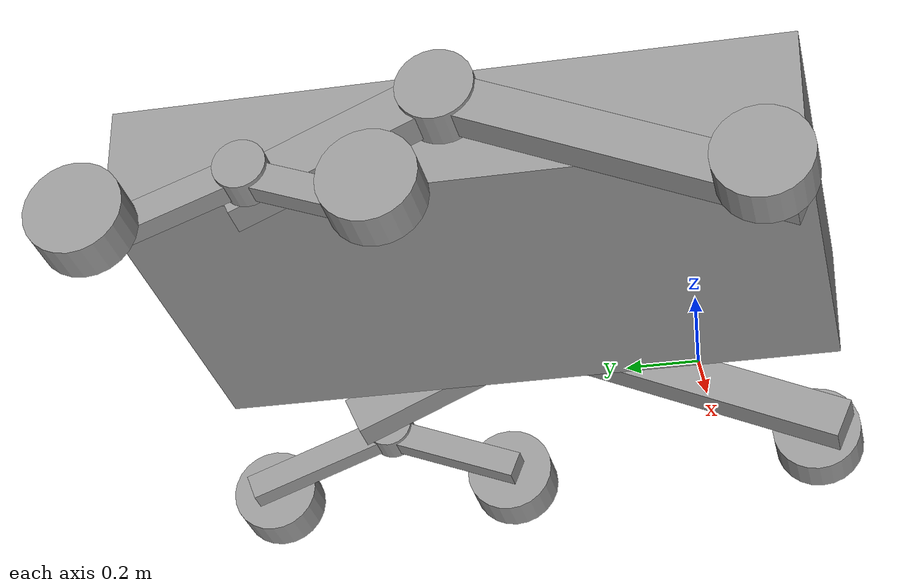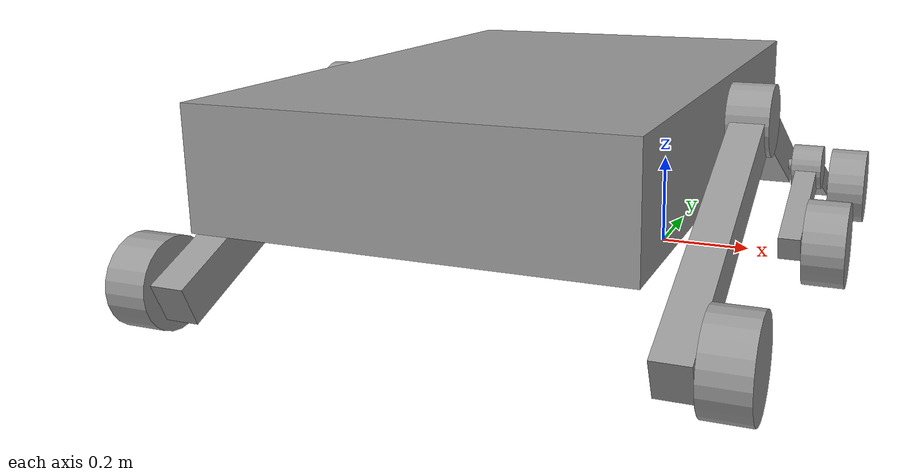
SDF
<?xml version='1.0'?>
<sdf version='1.6'>
  <model name='rover_2018'>
    <link name='main_chassis'>
      <pose frame=''>-0.495954 0.481744 0.172621 0 -0 0</pose>
      <inertial>
        <mass>10</mass>
        <inertia>
          <ixx>0.01</ixx>
          <ixy>0</ixy>
          <ixz>0</ixz>
          <iyy>0.01</iyy>
          <iyz>0</iyz>
          <izz>0.01</izz>
        </inertia>
        <pose frame=''>0 0 0 0 -0 0</pose>
      </inertial>
      <self_collide>0</self_collide>
      <kinematic>0</kinematic>
      <enable_wind>0</enable_wind>
      <visual name='visual'>
        <pose frame=''>0 0 0 0 -0 0</pose>
        <geometry>
          <box>
            <size>1.09569 1.7415 0.312322</size>
          </box>
        </geometry>
        <material>
          <lighting>1</lighting>
          <script>
            <uri>file://media/materials/scripts/gazebo.material</uri>
            <name>Gazebo/Grey</name>
          </script>
          <ambient>0.3 0.3 0.3 1</ambient>
          <diffuse>0.7 0.7 0.7 1</diffuse>
          <specular>0.01 0.01 0.01 1</specular>
          <emissive>0 0 0 1</emissive>
          <shader type='vertex'>
            <normal_map>__default__</normal_map>
          </shader>
        </material>
        <cast_shadows>1</cast_shadows>
        <transparency>0</transparency>
      </visual>
      <collision name='collision'>
        <laser_retro>0</laser_retro>
        <max_contacts>10</max_contacts>
        <pose frame=''>0 0 0 0 -0 0</pose>
        <geometry>
          <box>
            <size>1.09569 1.7415 0.312322</size>
          </box>
        </geometry>
        <surface>
          <friction>
            <ode>
              <mu>1</mu>
              <mu2>1</mu2>
              <fdir1>0 0 0</fdir1>
              <slip1>0</slip1>
              <slip2>0</slip2>
            </ode>
            <torsional>
              <coefficient>1</coefficient>
              <patch_radius>0</patch_radius>
              <surface_radius>0</surface_radius>
              <use_patch_radius>1</use_patch_radius>
              <ode>
                <slip>0</slip>
              </ode>
            </torsional>
          </friction>
          <bounce>
            <restitution_coefficient>0</restitution_coefficient>
            <threshold>1e+06</threshold>
          </bounce>
          <contact>
            <collide_without_contact>0</collide_without_contact>
            <collide_without_contact_bitmask>1</collide_without_contact_bitmask>
            <collide_bitmask>1</collide_bitmask>
            <ode>
              <soft_cfm>0</soft_cfm>
              <soft_erp>0.2</soft_erp>
              <kp>1e+13</kp>
              <kd>1</kd>
              <max_vel>0.01</max_vel>
              <min_depth>0</min_depth>
            </ode>
            <bullet>
              <split_impulse>1</split_impulse>
              <split_impulse_penetration_threshold>-0.01</split_impulse_penetration_threshold>
              <soft_cfm>0</soft_cfm>
              <soft_erp>0.2</soft_erp>
              <kp>1e+13</kp>
              <kd>1</kd>
            </bullet>
          </contact>
        </surface>
      </collision>
    </link>
    <link name='L_primary_rocker'>
      <pose frame=''>0.120732 0.480291 0.210888 3.14159 -1.57 -3.14159</pose>
      <inertial>
        <mass>0.0046174</mass>
        <inertia>
          <ixx>0.01</ixx>
          <ixy>0</ixy>
          <ixz>0</ixz>
          <iyy>0.01</iyy>
          <iyz>0</iyz>
          <izz>0.01</izz>
        </inertia>
        <pose frame=''>0 0 0 0 -0 0</pose>
      </inertial>
      <self_collide>0</self_collide>
      <kinematic>0</kinematic>
      <enable_wind>0</enable_wind>
      <visual name='visual'>
        <pose frame=''>0 0 0 0 -0 0</pose>
        <geometry>
          <cylinder>
            <radius>0.0992866</radius>
            <length>0.116478</length>
          </cylinder>
        </geometry>
        <material>
          <lighting>1</lighting>
          <script>
            <uri>file://media/materials/scripts/gazebo.material</uri>
            <name>Gazebo/Grey</name>
          </script>
          <ambient>0.3 0.3 0.3 1</ambient>
          <diffuse>0.7 0.7 0.7 1</diffuse>
          <specular>0.01 0.01 0.01 1</specular>
          <emissive>0 0 0 1</emissive>
          <shader type='vertex'>
            <normal_map>__default__</normal_map>
          </shader>
        </material>
        <cast_shadows>1</cast_shadows>
        <transparency>0</transparency>
      </visual>
    </link>
    <link name='L_primary_rocker_hinge'>
      <pose frame=''>0.045335 0.475634 0.210685 3.14159 -1.57 -3.14159</pose>
      <inertial>
        <mass>0.00110726</mass>
        <inertia>
          <ixx>0.01</ixx>
          <ixy>0</ixy>
          <ixz>0</ixz>
          <iyy>0.01</iyy>
          <iyz>0</iyz>
          <izz>0.01</izz>
        </inertia>
        <pose frame=''>0 0 0 0 -0 0</pose>
      </inertial>
      <self_collide>0</self_collide>
      <kinematic>0</kinematic>
      <enable_wind>0</enable_wind>
      <visual name='visual'>
        <pose frame=''>0 0 0 0 -0 0</pose>
        <geometry>
          <cylinder>
            <radius>0.0379471</radius>
            <length>0.191181</length>
          </cylinder>
        </geometry>
        <material>
          <lighting>1</lighting>
          <script>
            <uri>file://media/materials/scripts/gazebo.material</uri>
            <name>Gazebo/Grey</name>
          </script>
          <ambient>0.3 0.3 0.3 1</ambient>
          <diffuse>0.7 0.7 0.7 1</diffuse>
          <specular>0.01 0.01 0.01 1</specular>
          <emissive>0 0 0 1</emissive>
          <shader type='vertex'>
            <normal_map>__default__</normal_map>
          </shader>
        </material>
        <cast_shadows>1</cast_shadows>
        <transparency>0</transparency>
      </visual>
    </link>
    <link name='L_primary_wheel_arm_backwards'>
      <pose frame=''>0.120732 0.773902 0.074463 -0.422885 0 0</pose>
      <inertial>
        <mass>0.00541225</mass>
        <inertia>
          <ixx>0.01</ixx>
          <ixy>0</ixy>
          <ixz>0</ixz>
          <iyy>0.01</iyy>
          <iyz>0</iyz>
          <izz>0.01</izz>
        </inertia>
        <pose frame=''>0 0 0 0 -0 0</pose>
      </inertial>
      <self_collide>0</self_collide>
      <kinematic>0</kinematic>
      <enable_wind>0</enable_wind>
      <gravity>1</gravity>
      <visual name='visual'>
        <pose frame=''>0 0 0 0 -0 0</pose>
        <geometry>
          <box>
            <size>0.093481 0.512407 0.11302</size>
          </box>
        </geometry>
        <material>
          <lighting>1</lighting>
          <script>
            <uri>file://media/materials/scripts/gazebo.material</uri>
            <name>Gazebo/Grey</name>
          </script>
          <ambient>0.3 0.3 0.3 1</ambient>
          <diffuse>0.7 0.7 0.7 1</diffuse>
          <specular>0.01 0.01 0.01 1</specular>
          <emissive>0 0 0 1</emissive>
          <shader type='pixel'>
            <normal_map>__default__</normal_map>
          </shader>
        </material>
        <cast_shadows>1</cast_shadows>
        <transparency>0</transparency>
      </visual>
      <collision name='collision'>
        <laser_retro>0</laser_retro>
        <max_contacts>10</max_contacts>
        <pose frame=''>0 0 0 0 -0 0</pose>
        <geometry>
          <box>
            <size>0.093481 0.512407 0.11302</size>
          </box>
        </geometry>
        <surface>
          <friction>
            <ode>
              <mu>1</mu>
              <mu2>1</mu2>
              <fdir1>0 0 0</fdir1>
              <slip1>0</slip1>
              <slip2>0</slip2>
            </ode>
            <torsional>
              <coefficient>1</coefficient>
              <patch_radius>0</patch_radius>
              <surface_radius>0</surface_radius>
              <use_patch_radius>1</use_patch_radius>
              <ode>
                <slip>0</slip>
              </ode>
            </torsional>
          </friction>
          <bounce>
            <restitution_coefficient>0</restitution_coefficient>
            <threshold>1e+06</threshold>
          </bounce>
          <contact>
            <collide_without_contact>0</collide_without_contact>
            <collide_without_contact_bitmask>1</collide_without_contact_bitmask>
            <collide_bitmask>1</collide_bitmask>
            <ode>
              <soft_cfm>0</soft_cfm>
              <soft_erp>0.2</soft_erp>
              <kp>1e+13</kp>
              <kd>1</kd>
              <max_vel>0.01</max_vel>
              <min_depth>0</min_depth>
            </ode>
            <bullet>
              <split_impulse>1</split_impulse>
              <split_impulse_penetration_threshold>-0.01</split_impulse_penetration_threshold>
              <soft_cfm>0</soft_cfm>
              <soft_erp>0.2</soft_erp>
              <kp>1e+13</kp>
              <kd>1</kd>
            </bullet>
          </contact>
        </surface>
      </collision>
    </link>
    <link name='L_primary_wheel_arm_forwards'>
      <pose frame=''>0.120732 0.030921 0.003788 0.410827 -0 0</pose>
      <inertial>
        <mass>0.00955178</mass>
        <inertia>
          <ixx>0.01</ixx>
          <ixy>0</ixy>
          <ixz>0</ixz>
          <iyy>0.01</iyy>
          <iyz>0</iyz>
          <izz>0.01</izz>
        </inertia>
        <pose frame=''>0 0 0 0 -0 0</pose>
      </inertial>
      <self_collide>0</self_collide>
      <kinematic>0</kinematic>
      <enable_wind>0</enable_wind>
      <visual name='visual'>
        <pose frame=''>0 0 0 0 -0 0</pose>
        <geometry>
          <box>
            <size>0.093481 0.904318 0.11302</size>
          </box>
        </geometry>
        <material>
          <lighting>1</lighting>
          <script>
            <uri>file://media/materials/scripts/gazebo.material</uri>
            <name>Gazebo/Grey</name>
          </script>
          <ambient>0.3 0.3 0.3 1</ambient>
          <diffuse>0.7 0.7 0.7 1</diffuse>
          <specular>0.01 0.01 0.01 1</specular>
          <emissive>0 0 0 1</emissive>
          <shader type='vertex'>
            <normal_map>__default__</normal_map>
          </shader>
        </material>
        <cast_shadows>1</cast_shadows>
        <transparency>0</transparency>
      </visual>
      <collision name='collision'>
        <laser_retro>0</laser_retro>
        <max_contacts>10</max_contacts>
        <pose frame=''>0 0 0 0 -0 0</pose>
        <geometry>
          <box>
            <size>0.093481 0.904318 0.11302</size>
          </box>
        </geometry>
        <surface>
          <friction>
            <ode>
              <mu>1</mu>
              <mu2>1</mu2>
              <fdir1>0 0 0</fdir1>
              <slip1>0</slip1>
              <slip2>0</slip2>
            </ode>
            <torsional>
              <coefficient>1</coefficient>
              <patch_radius>0</patch_radius>
              <surface_radius>0</surface_radius>
              <use_patch_radius>1</use_patch_radius>
              <ode>
                <slip>0</slip>
              </ode>
            </torsional>
          </friction>
          <bounce>
            <restitution_coefficient>0</restitution_coefficient>
            <threshold>1e+06</threshold>
          </bounce>
          <contact>
            <collide_without_contact>0</collide_without_contact>
            <collide_without_contact_bitmask>1</collide_without_contact_bitmask>
            <collide_bitmask>1</collide_bitmask>
            <ode>
              <soft_cfm>0</soft_cfm>
              <soft_erp>0.2</soft_erp>
              <kp>1e+13</kp>
              <kd>1</kd>
              <max_vel>0.01</max_vel>
              <min_depth>0</min_depth>
            </ode>
            <bullet>
              <split_impulse>1</split_impulse>
              <split_impulse_penetration_threshold>-0.01</split_impulse_penetration_threshold>
              <soft_cfm>0</soft_cfm>
              <soft_erp>0.2</soft_erp>
              <kp>1e+13</kp>
              <kd>1</kd>
            </bullet>
          </contact>
        </surface>
      </collision>
    </link>
    <link name='L_secondary_rocker'>
      <pose frame=''>0.227534 0.930061 -0.012476 3.14159 -1.57 -3.14159</pose>
      <inertial>
        <mass>0.00158531</mass>
        <inertia>
          <ixx>0.01</ixx>
          <ixy>0</ixy>
          <ixz>0</ixz>
          <iyy>0.01</iyy>
          <iyz>0</iyz>
          <izz>0.01</izz>
        </inertia>
        <pose frame=''>0 0 0 0 -0 0</pose>
      </inertial>
      <self_collide>0</self_collide>
      <kinematic>0</kinematic>
      <enable_wind>0</enable_wind>
      <gravity>1</gravity>
      <visual name='visual'>
        <pose frame=''>0 0 0 0 -0 0</pose>
        <geometry>
          <cylinder>
            <radius>0.0665773</radius>
            <length>0.088915</length>
          </cylinder>
        </geometry>
        <material>
          <lighting>1</lighting>
          <script>
            <uri>file://media/materials/scripts/gazebo.material</uri>
            <name>Gazebo/Grey</name>
          </script>
          <ambient>0.3 0.3 0.3 1</ambient>
          <diffuse>0.7 0.7 0.7 1</diffuse>
          <specular>0.01 0.01 0.01 1</specular>
          <emissive>0 0 0 1</emissive>
          <shader type='vertex'>
            <normal_map>__default__</normal_map>
          </shader>
        </material>
        <cast_shadows>1</cast_shadows>
        <transparency>0</transparency>
      </visual>
    </link>
    <link name='L_secondary_rocker_hinge'>
      <pose frame=''>0.173471 0.937461 -0.010085 3.14159 -1.57 -3.14159</pose>
      <inertial>
        <mass>0.00016166</mass>
        <inertia>
          <ixx>0.01</ixx>
          <ixy>0</ixy>
          <ixz>0</ixz>
          <iyy>0.01</iyy>
          <iyz>0</iyz>
          <izz>0.01</izz>
        </inertia>
        <pose frame=''>0 0 0 0 -0 0</pose>
      </inertial>
      <self_collide>0</self_collide>
      <kinematic>0</kinematic>
      <gravity>1</gravity>
      <enable_wind>0</enable_wind>
      <visual name='visual'>
        <pose frame=''>0 0 0 0 -0 0</pose>
        <geometry>
          <cylinder>
            <radius>0.0152481</radius>
            <length>0.138038</length>
          </cylinder>
        </geometry>
        <material>
          <lighting>1</lighting>
          <script>
            <uri>file://media/materials/scripts/gazebo.material</uri>
            <name>Gazebo/Grey</name>
          </script>
          <ambient>0.3 0.3 0.3 1</ambient>
          <diffuse>0.7 0.7 0.7 1</diffuse>
          <specular>0.01 0.01 0.01 1</specular>
          <emissive>0 0 0 1</emissive>
          <shader type='vertex'>
            <normal_map>__default__</normal_map>
          </shader>
        </material>
        <cast_shadows>1</cast_shadows>
        <transparency>0</transparency>
      </visual>
    </link>
    <link name='L_secondary_wheel_arm_backwards'>
      <pose frame=''>0.227534 1.14505 -0.096467 -0.359364 0 0</pose>
      <inertial>
        <mass>0.0019482</mass>
        <inertia>
          <ixx>0.01</ixx>
          <ixy>0</ixy>
          <ixz>0</ixz>
          <iyy>0.01</iyy>
          <iyz>0</iyz>
          <izz>0.01</izz>
        </inertia>
        <pose frame=''>0 0 0 0 -0 0</pose>
      </inertial>
      <self_collide>0</self_collide>
      <kinematic>0</kinematic>
      <enable_wind>0</enable_wind>
      <visual name='visual'>
        <pose frame=''>0 0 0 0 -0 0</pose>
        <geometry>
          <box>
            <size>0.062968 0.419703 0.073703</size>
          </box>
        </geometry>
        <material>
          <lighting>1</lighting>
          <script>
            <uri>file://media/materials/scripts/gazebo.material</uri>
            <name>Gazebo/Grey</name>
          </script>
          <ambient>0.3 0.3 0.3 1</ambient>
          <diffuse>0.7 0.7 0.7 1</diffuse>
          <specular>0.01 0.01 0.01 1</specular>
          <emissive>0 0 0 1</emissive>
          <shader type='pixel'/>
        </material>
        <cast_shadows>1</cast_shadows>
        <transparency>0</transparency>
      </visual>
      <collision name='collision'>
        <laser_retro>0</laser_retro>
        <max_contacts>10</max_contacts>
        <pose frame=''>0 0 0 0 -0 0</pose>
        <geometry>
          <box>
            <size>0.062968 0.419703 0.073703</size>
          </box>
        </geometry>
        <surface>
          <friction>
            <ode>
              <mu>1</mu>
              <mu2>1</mu2>
              <fdir1>0 0 0</fdir1>
              <slip1>0</slip1>
              <slip2>0</slip2>
            </ode>
            <torsional>
              <coefficient>1</coefficient>
              <patch_radius>0</patch_radius>
              <surface_radius>0</surface_radius>
              <use_patch_radius>1</use_patch_radius>
              <ode>
                <slip>0</slip>
              </ode>
            </torsional>
          </friction>
          <bounce>
            <restitution_coefficient>0</restitution_coefficient>
            <threshold>1e+06</threshold>
          </bounce>
          <contact>
            <collide_without_contact>0</collide_without_contact>
            <collide_without_contact_bitmask>1</collide_without_contact_bitmask>
            <collide_bitmask>1</collide_bitmask>
            <ode>
              <soft_cfm>0</soft_cfm>
              <soft_erp>0.2</soft_erp>
              <kp>1e+13</kp>
              <kd>1</kd>
              <max_vel>0.01</max_vel>
              <min_depth>0</min_depth>
            </ode>
            <bullet>
              <split_impulse>1</split_impulse>
              <split_impulse_penetration_threshold>-0.01</split_impulse_penetration_threshold>
              <soft_cfm>0</soft_cfm>
              <soft_erp>0.2</soft_erp>
              <kp>1e+13</kp>
              <kd>1</kd>
            </bullet>
          </contact>
        </surface>
      </collision>
    </link>
    <link name='L_secondary_wheel_arm_forward'>
      <pose frame=''>0.227534 0.747337 -0.096816 0.366679 -0 0</pose>
      <inertial>
        <mass>0.00190054</mass>
        <inertia>
          <ixx>0.01</ixx>
          <ixy>0</ixy>
          <ixz>0</ixz>
          <iyy>0.01</iyy>
          <iyz>0</iyz>
          <izz>0.01</izz>
        </inertia>
        <pose frame=''>0 0 0 0 -0 0</pose>
      </inertial>
      <self_collide>0</self_collide>
      <kinematic>0</kinematic>
      <enable_wind>0</enable_wind>
      <visual name='visual'>
        <pose frame=''>0 0 0 0 -0 0</pose>
        <geometry>
          <box>
            <size>0.062968 0.40946 0.073703</size>
          </box>
        </geometry>
        <material>
          <lighting>1</lighting>
          <script>
            <uri>file://media/materials/scripts/gazebo.material</uri>
            <name>Gazebo/Grey</name>
          </script>
          <ambient>0.3 0.3 0.3 1</ambient>
          <diffuse>0.7 0.7 0.7 1</diffuse>
          <specular>0.01 0.01 0.01 1</specular>
          <emissive>0 0 0 1</emissive>
          <shader type='pixel'>
            <normal_map>__default__</normal_map>
          </shader>
        </material>
        <cast_shadows>1</cast_shadows>
        <transparency>0</transparency>
      </visual>
      <collision name='collision'>
        <laser_retro>0</laser_retro>
        <max_contacts>10</max_contacts>
        <pose frame=''>0 0 0 0 -0 0</pose>
        <geometry>
          <box>
            <size>0.062968 0.40946 0.073703</size>
          </box>
        </geometry>
        <surface>
          <friction>
            <ode>
              <mu>1</mu>
              <mu2>1</mu2>
              <fdir1>0 0 0</fdir1>
              <slip1>0</slip1>
              <slip2>0</slip2>
            </ode>
            <torsional>
              <coefficient>1</coefficient>
              <patch_radius>0</patch_radius>
              <surface_radius>0</surface_radius>
              <use_patch_radius>1</use_patch_radius>
              <ode>
                <slip>0</slip>
              </ode>
            </torsional>
          </friction>
          <bounce>
            <restitution_coefficient>0</restitution_coefficient>
            <threshold>1e+06</threshold>
          </bounce>
          <contact>
            <collide_without_contact>0</collide_without_contact>
            <collide_without_contact_bitmask>1</collide_without_contact_bitmask>
            <collide_bitmask>1</collide_bitmask>
            <ode>
              <soft_cfm>0</soft_cfm>
              <soft_erp>0.2</soft_erp>
              <kp>1e+13</kp>
              <kd>1</kd>
              <max_vel>0.01</max_vel>
              <min_depth>0</min_depth>
            </ode>
            <bullet>
              <split_impulse>1</split_impulse>
              <split_impulse_penetration_threshold>-0.01</split_impulse_penetration_threshold>
              <soft_cfm>0</soft_cfm>
              <soft_erp>0.2</soft_erp>
              <kp>1e+13</kp>
              <kd>1</kd>
            </bullet>
          </contact>
        </surface>
      </collision>
    </link>
    <link name='L_wheel_1'>
      <pose frame=''>0.231981 -0.300898 -0.152796 3.14159 -1.57 -3.14159</pose>
      <inertial>
        <mass>1</mass>
        <inertia>
          <ixx>0.01</ixx>
          <ixy>0</ixy>
          <ixz>0</ixz>
          <iyy>0.01</iyy>
          <iyz>0</iyz>
          <izz>0.01</izz>
        </inertia>
        <pose frame=''>0 0 0 0 -0 0</pose>
      </inertial>
      <self_collide>0</self_collide>
      <kinematic>0</kinematic>
      <enable_wind>0</enable_wind>
      <visual name='visual'>
        <pose frame=''>0 0 0 0 -0 0</pose>
        <geometry>
          <cylinder>
            <radius>0.122078</radius>
            <length>0.116478</length>
          </cylinder>
        </geometry>
        <material>
          <lighting>1</lighting>
          <script>
            <uri>file://media/materials/scripts/gazebo.material</uri>
            <name>Gazebo/Grey</name>
          </script>
          <ambient>0.3 0.3 0.3 1</ambient>
          <diffuse>0.7 0.7 0.7 1</diffuse>
          <specular>0.01 0.01 0.01 1</specular>
          <emissive>0 0 0 1</emissive>
          <shader type='vertex'>
            <normal_map>__default__</normal_map>
          </shader>
        </material>
        <cast_shadows>1</cast_shadows>
        <transparency>0</transparency>
      </visual>
      <collision name='collision'>
        <laser_retro>0</laser_retro>
        <max_contacts>10</max_contacts>
        <pose frame=''>0 0 0 0 -0 0</pose>
        <geometry>
          <cylinder>
            <radius>0.122078</radius>
            <length>0.116478</length>
          </cylinder>
        </geometry>
        <surface>
          <friction>
            <ode>
              <mu>1</mu>
              <mu2>1</mu2>
              <fdir1>0 0 0</fdir1>
              <slip1>0</slip1>
              <slip2>0</slip2>
            </ode>
            <torsional>
              <coefficient>1</coefficient>
              <patch_radius>0</patch_radius>
              <surface_radius>0</surface_radius>
              <use_patch_radius>1</use_patch_radius>
              <ode>
                <slip>0</slip>
              </ode>
            </torsional>
          </friction>
          <bounce>
            <restitution_coefficient>0</restitution_coefficient>
            <threshold>1e+06</threshold>
          </bounce>
          <contact>
            <collide_without_contact>0</collide_without_contact>
            <collide_without_contact_bitmask>1</collide_without_contact_bitmask>
            <collide_bitmask>1</collide_bitmask>
            <ode>
              <soft_cfm>0</soft_cfm>
              <soft_erp>0.2</soft_erp>
              <kp>1e+13</kp>
              <kd>1</kd>
              <max_vel>0.01</max_vel>
              <min_depth>0</min_depth>
            </ode>
            <bullet>
              <split_impulse>1</split_impulse>
              <split_impulse_penetration_threshold>-0.01</split_impulse_penetration_threshold>
              <soft_cfm>0</soft_cfm>
              <soft_erp>0.2</soft_erp>
              <kp>1e+13</kp>
              <kd>1</kd>
            </bullet>
          </contact>
        </surface>
      </collision>
    </link>
    <link name='L_wheel_2'>
      <pose frame=''>0.327595 0.588491 -0.15151 3.14159 -1.57 -3.14159</pose>
      <inertial>
        <mass>1</mass>
        <inertia>
          <ixx>0.01</ixx>
          <ixy>0</ixy>
          <ixz>0</ixz>
          <iyy>0.01</iyy>
          <iyz>0</iyz>
          <izz>0.01</izz>
        </inertia>
        <pose frame=''>0 0 0 0 -0 0</pose>
      </inertial>
      <self_collide>0</self_collide>
      <kinematic>0</kinematic>
      <enable_wind>0</enable_wind>
      <visual name='visual'>
        <pose frame=''>0 0 0 0 -0 0</pose>
        <geometry>
          <cylinder>
            <radius>0.122078</radius>
            <length>0.116478</length>
          </cylinder>
        </geometry>
        <material>
          <lighting>1</lighting>
          <script>
            <uri>file://media/materials/scripts/gazebo.material</uri>
            <name>Gazebo/Grey</name>
          </script>
          <ambient>0.3 0.3 0.3 1</ambient>
          <diffuse>0.7 0.7 0.7 1</diffuse>
          <specular>0.01 0.01 0.01 1</specular>
          <emissive>0 0 0 1</emissive>
          <shader type='vertex'>
            <normal_map>__default__</normal_map>
          </shader>
        </material>
        <cast_shadows>1</cast_shadows>
        <transparency>0</transparency>
      </visual>
      <collision name='collision'>
        <laser_retro>0</laser_retro>
        <max_contacts>10</max_contacts>
        <pose frame=''>0 0 0 0 -0 0</pose>
        <geometry>
          <cylinder>
            <radius>0.122078</radius>
            <length>0.116478</length>
          </cylinder>
        </geometry>
        <surface>
          <friction>
            <ode>
              <mu>1</mu>
              <mu2>1</mu2>
              <fdir1>0 0 0</fdir1>
              <slip1>0</slip1>
              <slip2>0</slip2>
            </ode>
            <torsional>
              <coefficient>1</coefficient>
              <patch_radius>0</patch_radius>
              <surface_radius>0</surface_radius>
              <use_patch_radius>1</use_patch_radius>
              <ode>
                <slip>0</slip>
              </ode>
            </torsional>
          </friction>
          <bounce>
            <restitution_coefficient>0</restitution_coefficient>
            <threshold>1e+06</threshold>
          </bounce>
          <contact>
            <collide_without_contact>0</collide_without_contact>
            <collide_without_contact_bitmask>1</collide_without_contact_bitmask>
            <collide_bitmask>1</collide_bitmask>
            <ode>
              <soft_cfm>0</soft_cfm>
              <soft_erp>0.2</soft_erp>
              <kp>1e+13</kp>
              <kd>1</kd>
              <max_vel>0.01</max_vel>
              <min_depth>0</min_depth>
            </ode>
            <bullet>
              <split_impulse>1</split_impulse>
              <split_impulse_penetration_threshold>-0.01</split_impulse_penetration_threshold>
              <soft_cfm>0</soft_cfm>
              <soft_erp>0.2</soft_erp>
              <kp>1e+13</kp>
              <kd>1</kd>
            </bullet>
          </contact>
        </surface>
      </collision>
    </link>
    <link name='L_wheel_3'>
      <pose frame=''>0.327595 1.29129 -0.152082 3.14159 -1.57 -3.14159</pose>
      <inertial>
        <mass>1</mass>
        <inertia>
          <ixx>0.01</ixx>
          <ixy>0</ixy>
          <ixz>0</ixz>
          <iyy>0.01</iyy>
          <iyz>0</iyz>
          <izz>0.01</izz>
        </inertia>
        <pose frame=''>0 0 0 0 -0 0</pose>
      </inertial>
      <self_collide>0</self_collide>
      <kinematic>0</kinematic>
      <enable_wind>0</enable_wind>
      <visual name='visual'>
        <pose frame=''>0 0 0 0 -0 0</pose>
        <geometry>
          <cylinder>
            <radius>0.122078</radius>
            <length>0.116478</length>
          </cylinder>
        </geometry>
        <material>
          <lighting>1</lighting>
          <script>
            <uri>file://media/materials/scripts/gazebo.material</uri>
            <name>Gazebo/Grey</name>
          </script>
          <ambient>0.3 0.3 0.3 1</ambient>
          <diffuse>0.7 0.7 0.7 1</diffuse>
          <specular>0.01 0.01 0.01 1</specular>
          <emissive>0 0 0 1</emissive>
          <shader type='vertex'>
            <normal_map>__default__</normal_map>
          </shader>
        </material>
        <cast_shadows>1</cast_shadows>
        <transparency>0</transparency>
      </visual>
      <collision name='collision'>
        <laser_retro>0</laser_retro>
        <max_contacts>10</max_contacts>
        <pose frame=''>0 0 0 0 -0 0</pose>
        <geometry>
          <cylinder>
            <radius>0.122078</radius>
            <length>0.116478</length>
          </cylinder>
        </geometry>
        <surface>
          <friction>
            <ode>
              <mu>1</mu>
              <mu2>1</mu2>
              <fdir1>0 0 0</fdir1>
              <slip1>0</slip1>
              <slip2>0</slip2>
            </ode>
            <torsional>
              <coefficient>1</coefficient>
              <patch_radius>0</patch_radius>
              <surface_radius>0</surface_radius>
              <use_patch_radius>1</use_patch_radius>
              <ode>
                <slip>0</slip>
              </ode>
            </torsional>
          </friction>
          <bounce>
            <restitution_coefficient>0</restitution_coefficient>
            <threshold>1e+06</threshold>
          </bounce>
          <contact>
            <collide_without_contact>0</collide_without_contact>
            <collide_without_contact_bitmask>1</collide_without_contact_bitmask>
            <collide_bitmask>1</collide_bitmask>
            <ode>
              <soft_cfm>0</soft_cfm>
              <soft_erp>0.2</soft_erp>
              <kp>1e+13</kp>
              <kd>1</kd>
              <max_vel>0.01</max_vel>
              <min_depth>0</min_depth>
            </ode>
            <bullet>
              <split_impulse>1</split_impulse>
              <split_impulse_penetration_threshold>-0.01</split_impulse_penetration_threshold>
              <soft_cfm>0</soft_cfm>
              <soft_erp>0.2</soft_erp>
              <kp>1e+13</kp>
              <kd>1</kd>
            </bullet>
          </contact>
        </surface>
      </collision>
    </link>
    <link name='L_wheel_hinge_1'>
      <pose frame=''>0.157404 -0.319861 -0.15619 3.14159 -1.57 -3.14159</pose>
      <inertial>
        <mass>0.00016166</mass>
        <inertia>
          <ixx>0.01</ixx>
          <ixy>0</ixy>
          <ixz>0</ixz>
          <iyy>0.01</iyy>
          <iyz>0</iyz>
          <izz>0.01</izz>
        </inertia>
        <pose frame=''>0 0 0 0 -0 0</pose>
      </inertial>
      <self_collide>0</self_collide>
      <kinematic>0</kinematic>
      <enable_wind>0</enable_wind>
      <visual name='visual'>
        <pose frame=''>0 0 0 0 -0 0</pose>
        <geometry>
          <cylinder>
            <radius>0.0170673</radius>
            <length>0.138038</length>
          </cylinder>
        </geometry>
        <material>
          <lighting>1</lighting>
          <script>
            <uri>file://media/materials/scripts/gazebo.material</uri>
            <name>Gazebo/Grey</name>
          </script>
          <ambient>0.3 0.3 0.3 1</ambient>
          <diffuse>0.7 0.7 0.7 1</diffuse>
          <specular>0.01 0.01 0.01 1</specular>
          <emissive>0 0 0 1</emissive>
          <shader type='vertex'>
            <normal_map>__default__</normal_map>
          </shader>
        </material>
        <cast_shadows>1</cast_shadows>
        <transparency>0</transparency>
      </visual>
    </link>
    <link name='L_wheel_hinge_2'>
      <pose frame=''>0.266627 0.591116 -0.159992 3.14159 -1.57 -3.14159</pose>
      <inertial>
        <mass>0.00016166</mass>
        <inertia>
          <ixx>0.01</ixx>
          <ixy>0</ixy>
          <ixz>0</ixz>
          <iyy>0.01</iyy>
          <iyz>0</iyz>
          <izz>0.01</izz>
        </inertia>
        <pose frame=''>0 0 0 0 -0 0</pose>
      </inertial>
      <self_collide>0</self_collide>
      <kinematic>0</kinematic>
      <enable_wind>0</enable_wind>
      <visual name='visual'>
        <pose frame=''>0 0 0 0 -0 0</pose>
        <geometry>
          <cylinder>
            <radius>0.0170673</radius>
            <length>0.138038</length>
          </cylinder>
        </geometry>
        <material>
          <lighting>1</lighting>
          <script>
            <uri>file://media/materials/scripts/gazebo.material</uri>
            <name>Gazebo/Grey</name>
          </script>
          <ambient>0.3 0.3 0.3 1</ambient>
          <diffuse>0.7 0.7 0.7 1</diffuse>
          <specular>0.01 0.01 0.01 1</specular>
          <emissive>0 0 0 1</emissive>
          <shader type='vertex'>
            <normal_map>__default__</normal_map>
          </shader>
        </material>
        <cast_shadows>1</cast_shadows>
        <transparency>0</transparency>
      </visual>
    </link>
    <link name='L_wheel_hinge_3'>
      <pose frame=''>0.283732 1.29534 -0.157563 3.14159 -1.57 -3.14159</pose>
      <inertial>
        <mass>0.0001415</mass>
        <inertia>
          <ixx>0.01</ixx>
          <ixy>0</ixy>
          <ixz>0</ixz>
          <iyy>0.01</iyy>
          <iyz>0</iyz>
          <izz>0.01</izz>
        </inertia>
        <pose frame=''>0 0 0 0 -0 0</pose>
      </inertial>
      <self_collide>0</self_collide>
      <kinematic>0</kinematic>
      <enable_wind>0</enable_wind>
      <visual name='visual'>
        <pose frame=''>0 0 0 0 -0 0</pose>
        <geometry>
          <cylinder>
            <radius>0.0170673</radius>
            <length>0.120823</length>
          </cylinder>
        </geometry>
        <material>
          <lighting>1</lighting>
          <script>
            <uri>file://media/materials/scripts/gazebo.material</uri>
            <name>Gazebo/Grey</name>
          </script>
          <ambient>0.3 0.3 0.3 1</ambient>
          <diffuse>0.7 0.7 0.7 1</diffuse>
          <specular>0.01 0.01 0.01 1</specular>
          <emissive>0 0 0 1</emissive>
          <shader type='vertex'>
            <normal_map>__default__</normal_map>
          </shader>
        </material>
        <cast_shadows>1</cast_shadows>
        <transparency>0</transparency>
      </visual>
    </link>
    <link name='R_primary_rocker'>
      <pose frame=''>-1.11994 0.480291 0.2099 3.14159 -1.57 -3.14159</pose>
      <inertial>
        <mass>0.0046174</mass>
        <inertia>
          <ixx>0.01</ixx>
          <ixy>0</ixy>
          <ixz>0</ixz>
          <iyy>0.01</iyy>
          <iyz>0</iyz>
          <izz>0.01</izz>
        </inertia>
        <pose frame=''>0 0 0 0 -0 0</pose>
      </inertial>
      <self_collide>0</self_collide>
      <kinematic>0</kinematic>
      <enable_wind>0</enable_wind>
      <visual name='visual'>
        <pose frame=''>0 0 0 0 -0 0</pose>
        <geometry>
          <cylinder>
            <radius>0.0992866</radius>
            <length>0.116478</length>
          </cylinder>
        </geometry>
        <material>
          <lighting>1</lighting>
          <script>
            <uri>file://media/materials/scripts/gazebo.material</uri>
            <name>Gazebo/Grey</name>
          </script>
          <ambient>0.3 0.3 0.3 1</ambient>
          <diffuse>0.7 0.7 0.7 1</diffuse>
          <specular>0.01 0.01 0.01 1</specular>
          <emissive>0 0 0 1</emissive>
          <shader type='vertex'>
            <normal_map>__default__</normal_map>
          </shader>
        </material>
        <cast_shadows>1</cast_shadows>
        <transparency>0</transparency>
      </visual>
    </link>
    <link name='R_primary_rocker_hinge'>
      <pose frame=''>-1.03751 0.475634 0.209823 3.14159 -1.57 -3.14159</pose>
      <inertial>
        <mass>0.00110726</mass>
        <inertia>
          <ixx>0.01</ixx>
          <ixy>0</ixy>
          <ixz>0</ixz>
          <iyy>0.01</iyy>
          <iyz>0</iyz>
          <izz>0.01</izz>
        </inertia>
        <pose frame=''>0 0 0 0 -0 0</pose>
      </inertial>
      <self_collide>0</self_collide>
      <kinematic>0</kinematic>
      <enable_wind>0</enable_wind>
      <visual name='visual'>
        <pose frame=''>0 0 0 0 -0 0</pose>
        <geometry>
          <cylinder>
            <radius>0.0379471</radius>
            <length>0.191181</length>
          </cylinder>
        </geometry>
        <material>
          <lighting>1</lighting>
          <script>
            <uri>file://media/materials/scripts/gazebo.material</uri>
            <name>Gazebo/Grey</name>
          </script>
          <ambient>0.3 0.3 0.3 1</ambient>
          <diffuse>0.7 0.7 0.7 1</diffuse>
          <specular>0.01 0.01 0.01 1</specular>
          <emissive>0 0 0 1</emissive>
          <shader type='vertex'>
            <normal_map>__default__</normal_map>
          </shader>
        </material>
        <cast_shadows>1</cast_shadows>
        <transparency>0</transparency>
      </visual>
    </link>
    <link name='R_primary_wheel_arm_backwards'>
      <pose frame=''>-1.11994 0.773902 0.074463 -0.422885 0 0</pose>
      <inertial>
        <mass>0.00541225</mass>
        <inertia>
          <ixx>0.01</ixx>
          <ixy>0</ixy>
          <ixz>0</ixz>
          <iyy>0.01</iyy>
          <iyz>0</iyz>
          <izz>0.01</izz>
        </inertia>
        <pose frame=''>0 0 0 0 -0 0</pose>
      </inertial>
      <self_collide>0</self_collide>
      <kinematic>0</kinematic>
      <enable_wind>0</enable_wind>
      <visual name='visual'>
        <pose frame=''>0 0 0 0 -0 0</pose>
        <geometry>
          <box>
            <size>0.093481 0.512407 0.11302</size>
          </box>
        </geometry>
        <material>
          <lighting>1</lighting>
          <script>
            <uri>file://media/materials/scripts/gazebo.material</uri>
            <name>Gazebo/Grey</name>
          </script>
          <ambient>0.3 0.3 0.3 1</ambient>
          <diffuse>0.7 0.7 0.7 1</diffuse>
          <specular>0.01 0.01 0.01 1</specular>
          <emissive>0 0 0 1</emissive>
          <shader type='pixel'/>
        </material>
        <cast_shadows>1</cast_shadows>
        <transparency>0</transparency>
      </visual>
      <collision name='collision'>
        <laser_retro>0</laser_retro>
        <max_contacts>10</max_contacts>
        <pose frame=''>0 0 0 0 -0 0</pose>
        <geometry>
          <box>
            <size>0.093481 0.512407 0.11302</size>
          </box>
        </geometry>
        <surface>
          <friction>
            <ode>
              <mu>1</mu>
              <mu2>1</mu2>
              <fdir1>0 0 0</fdir1>
              <slip1>0</slip1>
              <slip2>0</slip2>
            </ode>
            <torsional>
              <coefficient>1</coefficient>
              <patch_radius>0</patch_radius>
              <surface_radius>0</surface_radius>
              <use_patch_radius>1</use_patch_radius>
              <ode>
                <slip>0</slip>
              </ode>
            </torsional>
          </friction>
          <bounce>
            <restitution_coefficient>0</restitution_coefficient>
            <threshold>1e+06</threshold>
          </bounce>
          <contact>
            <collide_without_contact>0</collide_without_contact>
            <collide_without_contact_bitmask>1</collide_without_contact_bitmask>
            <collide_bitmask>1</collide_bitmask>
            <ode>
              <soft_cfm>0</soft_cfm>
              <soft_erp>0.2</soft_erp>
              <kp>1e+13</kp>
              <kd>1</kd>
              <max_vel>0.01</max_vel>
              <min_depth>0</min_depth>
            </ode>
            <bullet>
              <split_impulse>1</split_impulse>
              <split_impulse_penetration_threshold>-0.01</split_impulse_penetration_threshold>
              <soft_cfm>0</soft_cfm>
              <soft_erp>0.2</soft_erp>
              <kp>1e+13</kp>
              <kd>1</kd>
            </bullet>
          </contact>
        </surface>
      </collision>
    </link>
    <link name='R_primary_wheel_arm_forwards'>
      <pose frame=''>-1.11994 0.030921 0.003788 0.410827 -0 0</pose>
      <inertial>
        <mass>0.00955178</mass>
        <inertia>
          <ixx>0.01</ixx>
          <ixy>0</ixy>
          <ixz>0</ixz>
          <iyy>0.01</iyy>
          <iyz>0</iyz>
          <izz>0.01</izz>
        </inertia>
        <pose frame=''>0 0 0 0 -0 0</pose>
      </inertial>
      <self_collide>0</self_collide>
      <kinematic>0</kinematic>
      <enable_wind>0</enable_wind>
      <visual name='visual'>
        <pose frame=''>0 0 0 0 -0 0</pose>
        <geometry>
          <box>
            <size>0.093481 0.904318 0.11302</size>
          </box>
        </geometry>
        <material>
          <lighting>1</lighting>
          <script>
            <uri>file://media/materials/scripts/gazebo.material</uri>
            <name>Gazebo/Grey</name>
          </script>
          <ambient>0.3 0.3 0.3 1</ambient>
          <diffuse>0.7 0.7 0.7 1</diffuse>
          <specular>0.01 0.01 0.01 1</specular>
          <emissive>0 0 0 1</emissive>
          <shader type='vertex'>
            <normal_map>__default__</normal_map>
          </shader>
        </material>
        <cast_shadows>1</cast_shadows>
        <transparency>0</transparency>
      </visual>
      <collision name='collision'>
        <laser_retro>0</laser_retro>
        <max_contacts>10</max_contacts>
        <pose frame=''>0 0 0 0 -0 0</pose>
        <geometry>
          <box>
            <size>0.093481 0.904318 0.11302</size>
          </box>
        </geometry>
        <surface>
          <friction>
            <ode>
              <mu>1</mu>
              <mu2>1</mu2>
              <fdir1>0 0 0</fdir1>
              <slip1>0</slip1>
              <slip2>0</slip2>
            </ode>
            <torsional>
              <coefficient>1</coefficient>
              <patch_radius>0</patch_radius>
              <surface_radius>0</surface_radius>
              <use_patch_radius>1</use_patch_radius>
              <ode>
                <slip>0</slip>
              </ode>
            </torsional>
          </friction>
          <bounce>
            <restitution_coefficient>0</restitution_coefficient>
            <threshold>1e+06</threshold>
          </bounce>
          <contact>
            <collide_without_contact>0</collide_without_contact>
            <collide_without_contact_bitmask>1</collide_without_contact_bitmask>
            <collide_bitmask>1</collide_bitmask>
            <ode>
              <soft_cfm>0</soft_cfm>
              <soft_erp>0.2</soft_erp>
              <kp>1e+13</kp>
              <kd>1</kd>
              <max_vel>0.01</max_vel>
              <min_depth>0</min_depth>
            </ode>
            <bullet>
              <split_impulse>1</split_impulse>
              <split_impulse_penetration_threshold>-0.01</split_impulse_penetration_threshold>
              <soft_cfm>0</soft_cfm>
              <soft_erp>0.2</soft_erp>
              <kp>1e+13</kp>
              <kd>1</kd>
            </bullet>
          </contact>
        </surface>
      </collision>
    </link>
    <link name='R_secondary_rocker'>
      <pose frame=''>-1.22452 0.930061 -0.013632 3.14159 -1.57 -3.14159</pose>
      <inertial>
        <mass>0.00158531</mass>
        <inertia>
          <ixx>0.01</ixx>
          <ixy>0</ixy>
          <ixz>0</ixz>
          <iyy>0.01</iyy>
          <iyz>0</iyz>
          <izz>0.01</izz>
        </inertia>
        <pose frame=''>0 0 0 0 -0 0</pose>
      </inertial>
      <self_collide>0</self_collide>
      <kinematic>0</kinematic>
      <enable_wind>0</enable_wind>
      <visual name='visual'>
        <pose frame=''>0 0 0 0 -0 0</pose>
        <geometry>
          <cylinder>
            <radius>0.0665773</radius>
            <length>0.088915</length>
          </cylinder>
        </geometry>
        <material>
          <lighting>1</lighting>
          <script>
            <uri>file://media/materials/scripts/gazebo.material</uri>
            <name>Gazebo/Grey</name>
          </script>
          <ambient>0.3 0.3 0.3 1</ambient>
          <diffuse>0.7 0.7 0.7 1</diffuse>
          <specular>0.01 0.01 0.01 1</specular>
          <emissive>0 0 0 1</emissive>
          <shader type='vertex'>
            <normal_map>__default__</normal_map>
          </shader>
        </material>
        <cast_shadows>1</cast_shadows>
        <transparency>0</transparency>
      </visual>
    </link>
    <link name='R_secondary_rocker_hinge'>
      <pose frame=''>-1.16913 0.937461 -0.011154 3.14159 -1.57 -3.14159</pose>
      <inertial>
        <mass>0.00016166</mass>
        <inertia>
          <ixx>0.01</ixx>
          <ixy>0</ixy>
          <ixz>0</ixz>
          <iyy>0.01</iyy>
          <iyz>0</iyz>
          <izz>0.01</izz>
        </inertia>
        <pose frame=''>0 0 0 0 -0 0</pose>
      </inertial>
      <self_collide>0</self_collide>
      <kinematic>0</kinematic>
      <enable_wind>0</enable_wind>
      <visual name='visual'>
        <pose frame=''>0 0 0 0 -0 0</pose>
        <geometry>
          <cylinder>
            <radius>0.0170673</radius>
            <length>0.138038</length>
          </cylinder>
        </geometry>
        <material>
          <lighting>1</lighting>
          <script>
            <uri>file://media/materials/scripts/gazebo.material</uri>
            <name>Gazebo/Grey</name>
          </script>
          <ambient>0.3 0.3 0.3 1</ambient>
          <diffuse>0.7 0.7 0.7 1</diffuse>
          <specular>0.01 0.01 0.01 1</specular>
          <emissive>0 0 0 1</emissive>
          <shader type='vertex'>
            <normal_map>__default__</normal_map>
          </shader>
        </material>
        <cast_shadows>1</cast_shadows>
        <transparency>0</transparency>
      </visual>
    </link>
    <link name='R_secondary_wheel_arm_backwards'>
      <pose frame=''>-1.22452 1.14505 -0.096467 -0.359364 0 0</pose>
      <inertial>
        <mass>0.0019482</mass>
        <inertia>
          <ixx>0.01</ixx>
          <ixy>0</ixy>
          <ixz>0</ixz>
          <iyy>0.01</iyy>
          <iyz>0</iyz>
          <izz>0.01</izz>
        </inertia>
        <pose frame=''>0 0 0 0 -0 0</pose>
      </inertial>
      <self_collide>0</self_collide>
      <kinematic>0</kinematic>
      <enable_wind>0</enable_wind>
      <visual name='visual'>
        <pose frame=''>0 0 0 0 -0 0</pose>
        <geometry>
          <box>
            <size>0.062968 0.419703 0.073703</size>
          </box>
        </geometry>
        <material>
          <lighting>1</lighting>
          <script>
            <uri>file://media/materials/scripts/gazebo.material</uri>
            <name>Gazebo/Grey</name>
          </script>
          <ambient>0.3 0.3 0.3 1</ambient>
          <diffuse>0.7 0.7 0.7 1</diffuse>
          <specular>0.01 0.01 0.01 1</specular>
          <emissive>0 0 0 1</emissive>
          <shader type='pixel'>
            <normal_map>__default__</normal_map>
          </shader>
        </material>
        <cast_shadows>1</cast_shadows>
        <transparency>0</transparency>
      </visual>
      <collision name='collision'>
        <laser_retro>0</laser_retro>
        <max_contacts>10</max_contacts>
        <pose frame=''>0 0 0 0 -0 0</pose>
        <geometry>
          <box>
            <size>0.062968 0.419703 0.073703</size>
          </box>
        </geometry>
        <surface>
          <friction>
            <ode>
              <mu>1</mu>
              <mu2>1</mu2>
              <fdir1>0 0 0</fdir1>
              <slip1>0</slip1>
              <slip2>0</slip2>
            </ode>
            <torsional>
              <coefficient>1</coefficient>
              <patch_radius>0</patch_radius>
              <surface_radius>0</surface_radius>
              <use_patch_radius>1</use_patch_radius>
              <ode>
                <slip>0</slip>
              </ode>
            </torsional>
          </friction>
          <bounce>
            <restitution_coefficient>0</restitution_coefficient>
            <threshold>1e+06</threshold>
          </bounce>
          <contact>
            <collide_without_contact>0</collide_without_contact>
            <collide_without_contact_bitmask>1</collide_without_contact_bitmask>
            <collide_bitmask>1</collide_bitmask>
            <ode>
              <soft_cfm>0</soft_cfm>
              <soft_erp>0.2</soft_erp>
              <kp>1e+13</kp>
              <kd>1</kd>
              <max_vel>0.01</max_vel>
              <min_depth>0</min_depth>
            </ode>
            <bullet>
              <split_impulse>1</split_impulse>
              <split_impulse_penetration_threshold>-0.01</split_impulse_penetration_threshold>
              <soft_cfm>0</soft_cfm>
              <soft_erp>0.2</soft_erp>
              <kp>1e+13</kp>
              <kd>1</kd>
            </bullet>
          </contact>
        </surface>
      </collision>
    </link>
    <link name='R_secondary_wheel_arm_forward'>
      <pose frame=''>-1.22452 0.747337 -0.096816 0.366679 -0 0</pose>
      <inertial>
        <mass>0.00190054</mass>
        <inertia>
          <ixx>0.01</ixx>
          <ixy>0</ixy>
          <ixz>0</ixz>
          <iyy>0.01</iyy>
          <iyz>0</iyz>
          <izz>0.01</izz>
        </inertia>
        <pose frame=''>0 0 0 0 -0 0</pose>
      </inertial>
      <self_collide>0</self_collide>
      <kinematic>0</kinematic>
      <enable_wind>0</enable_wind>
      <visual name='visual'>
        <pose frame=''>0 0 0 0 -0 0</pose>
        <geometry>
          <box>
            <size>0.062968 0.40946 0.073703</size>
          </box>
        </geometry>
        <material>
          <lighting>1</lighting>
          <script>
            <uri>file://media/materials/scripts/gazebo.material</uri>
            <name>Gazebo/Grey</name>
          </script>
          <ambient>0.3 0.3 0.3 1</ambient>
          <diffuse>0.7 0.7 0.7 1</diffuse>
          <specular>0.01 0.01 0.01 1</specular>
          <emissive>0 0 0 1</emissive>
          <shader type='pixel'>
            <normal_map>__default__</normal_map>
          </shader>
        </material>
        <cast_shadows>1</cast_shadows>
        <transparency>0</transparency>
      </visual>
      <collision name='collision'>
        <laser_retro>0</laser_retro>
        <max_contacts>10</max_contacts>
        <pose frame=''>0 0 0 0 -0 0</pose>
        <geometry>
          <box>
            <size>0.062968 0.40946 0.073703</size>
          </box>
        </geometry>
        <surface>
          <friction>
            <ode>
              <mu>1</mu>
              <mu2>1</mu2>
              <fdir1>0 0 0</fdir1>
              <slip1>0</slip1>
              <slip2>0</slip2>
            </ode>
            <torsional>
              <coefficient>1</coefficient>
              <patch_radius>0</patch_radius>
              <surface_radius>0</surface_radius>
              <use_patch_radius>1</use_patch_radius>
              <ode>
                <slip>0</slip>
              </ode>
            </torsional>
          </friction>
          <bounce>
            <restitution_coefficient>0</restitution_coefficient>
            <threshold>1e+06</threshold>
          </bounce>
          <contact>
            <collide_without_contact>0</collide_without_contact>
            <collide_without_contact_bitmask>1</collide_without_contact_bitmask>
            <collide_bitmask>1</collide_bitmask>
            <ode>
              <soft_cfm>0</soft_cfm>
              <soft_erp>0.2</soft_erp>
              <kp>1e+13</kp>
              <kd>1</kd>
              <max_vel>0.01</max_vel>
              <min_depth>0</min_depth>
            </ode>
            <bullet>
              <split_impulse>1</split_impulse>
              <split_impulse_penetration_threshold>-0.01</split_impulse_penetration_threshold>
              <soft_cfm>0</soft_cfm>
              <soft_erp>0.2</soft_erp>
              <kp>1e+13</kp>
              <kd>1</kd>
            </bullet>
          </contact>
        </surface>
      </collision>
    </link>
    <link name='R_wheel_1'>
      <pose frame=''>-1.23345 -0.300898 -0.153963 3.14159 -1.57 -3.14159</pose>
      <inertial>
        <mass>1</mass>
        <inertia>
          <ixx>0.01</ixx>
          <ixy>0</ixy>
          <ixz>0</ixz>
          <iyy>0.01</iyy>
          <iyz>0</iyz>
          <izz>0.01</izz>
        </inertia>
        <pose frame=''>0 0 0 0 -0 0</pose>
      </inertial>
      <self_collide>0</self_collide>
      <kinematic>0</kinematic>
      <enable_wind>0</enable_wind>
      <visual name='visual'>
        <pose frame=''>0 0 0 0 -0 0</pose>
        <geometry>
          <cylinder>
            <radius>0.122078</radius>
            <length>0.116478</length>
          </cylinder>
        </geometry>
        <material>
          <lighting>1</lighting>
          <script>
            <uri>file://media/materials/scripts/gazebo.material</uri>
            <name>Gazebo/Grey</name>
          </script>
          <ambient>0.3 0.3 0.3 1</ambient>
          <diffuse>0.7 0.7 0.7 1</diffuse>
          <specular>0.01 0.01 0.01 1</specular>
          <emissive>0 0 0 1</emissive>
          <shader type='vertex'>
            <normal_map>__default__</normal_map>
          </shader>
        </material>
        <cast_shadows>1</cast_shadows>
        <transparency>0</transparency>
      </visual>
      <collision name='collision'>
        <laser_retro>0</laser_retro>
        <max_contacts>10</max_contacts>
        <pose frame=''>0 0 0 0 -0 0</pose>
        <geometry>
          <cylinder>
            <radius>0.122078</radius>
            <length>0.116478</length>
          </cylinder>
        </geometry>
        <surface>
          <friction>
            <ode>
              <mu>1</mu>
              <mu2>1</mu2>
              <fdir1>0 0 0</fdir1>
              <slip1>0</slip1>
              <slip2>0</slip2>
            </ode>
            <torsional>
              <coefficient>1</coefficient>
              <patch_radius>0</patch_radius>
              <surface_radius>0</surface_radius>
              <use_patch_radius>1</use_patch_radius>
              <ode>
                <slip>0</slip>
              </ode>
            </torsional>
          </friction>
          <bounce>
            <restitution_coefficient>0</restitution_coefficient>
            <threshold>1e+06</threshold>
          </bounce>
          <contact>
            <collide_without_contact>0</collide_without_contact>
            <collide_without_contact_bitmask>1</collide_without_contact_bitmask>
            <collide_bitmask>1</collide_bitmask>
            <ode>
              <soft_cfm>0</soft_cfm>
              <soft_erp>0.2</soft_erp>
              <kp>1e+13</kp>
              <kd>1</kd>
              <max_vel>0.01</max_vel>
              <min_depth>0</min_depth>
            </ode>
            <bullet>
              <split_impulse>1</split_impulse>
              <split_impulse_penetration_threshold>-0.01</split_impulse_penetration_threshold>
              <soft_cfm>0</soft_cfm>
              <soft_erp>0.2</soft_erp>
              <kp>1e+13</kp>
              <kd>1</kd>
            </bullet>
          </contact>
        </surface>
      </collision>
    </link>
    <link name='R_wheel_2'>
      <pose frame=''>-1.31728 0.588299 -0.152822 3.14159 -1.57 -3.14159</pose>
      <inertial>
        <mass>1</mass>
        <inertia>
          <ixx>0.01</ixx>
          <ixy>0</ixy>
          <ixz>0</ixz>
          <iyy>0.01</iyy>
          <iyz>0</iyz>
          <izz>0.01</izz>
        </inertia>
        <pose frame=''>0 0 0 0 -0 0</pose>
      </inertial>
      <self_collide>0</self_collide>
      <kinematic>0</kinematic>
      <enable_wind>0</enable_wind>
      <visual name='visual'>
        <pose frame=''>0 0 0 0 -0 0</pose>
        <geometry>
          <cylinder>
            <radius>0.122078</radius>
            <length>0.116478</length>
          </cylinder>
        </geometry>
        <material>
          <lighting>1</lighting>
          <script>
            <uri>file://media/materials/scripts/gazebo.material</uri>
            <name>Gazebo/Grey</name>
          </script>
          <ambient>0.3 0.3 0.3 1</ambient>
          <diffuse>0.7 0.7 0.7 1</diffuse>
          <specular>0.01 0.01 0.01 1</specular>
          <emissive>0 0 0 1</emissive>
          <shader type='vertex'>
            <normal_map>__default__</normal_map>
          </shader>
        </material>
        <cast_shadows>1</cast_shadows>
        <transparency>0</transparency>
      </visual>
      <collision name='collision'>
        <laser_retro>0</laser_retro>
        <max_contacts>10</max_contacts>
        <pose frame=''>0 0 0 0 -0 0</pose>
        <geometry>
          <cylinder>
            <radius>0.122078</radius>
            <length>0.116478</length>
          </cylinder>
        </geometry>
        <surface>
          <friction>
            <ode>
              <mu>1</mu>
              <mu2>1</mu2>
              <fdir1>0 0 0</fdir1>
              <slip1>0</slip1>
              <slip2>0</slip2>
            </ode>
            <torsional>
              <coefficient>1</coefficient>
              <patch_radius>0</patch_radius>
              <surface_radius>0</surface_radius>
              <use_patch_radius>1</use_patch_radius>
              <ode>
                <slip>0</slip>
              </ode>
            </torsional>
          </friction>
          <bounce>
            <restitution_coefficient>0</restitution_coefficient>
            <threshold>1e+06</threshold>
          </bounce>
          <contact>
            <collide_without_contact>0</collide_without_contact>
            <collide_without_contact_bitmask>1</collide_without_contact_bitmask>
            <collide_bitmask>1</collide_bitmask>
            <ode>
              <soft_cfm>0</soft_cfm>
              <soft_erp>0.2</soft_erp>
              <kp>1e+13</kp>
              <kd>1</kd>
              <max_vel>0.01</max_vel>
              <min_depth>0</min_depth>
            </ode>
            <bullet>
              <split_impulse>1</split_impulse>
              <split_impulse_penetration_threshold>-0.01</split_impulse_penetration_threshold>
              <soft_cfm>0</soft_cfm>
              <soft_erp>0.2</soft_erp>
              <kp>1e+13</kp>
              <kd>1</kd>
            </bullet>
          </contact>
        </surface>
      </collision>
    </link>
    <link name='R_wheel_3'>
      <pose frame=''>-1.31997 1.29129 -0.1534 3.14159 -1.57 -3.14159</pose>
      <inertial>
        <mass>1</mass>
        <inertia>
          <ixx>0.01</ixx>
          <ixy>0</ixy>
          <ixz>0</ixz>
          <iyy>0.01</iyy>
          <iyz>0</iyz>
          <izz>0.01</izz>
        </inertia>
        <pose frame=''>0 0 0 0 -0 0</pose>
      </inertial>
      <self_collide>0</self_collide>
      <kinematic>0</kinematic>
      <enable_wind>0</enable_wind>
      <visual name='visual'>
        <pose frame=''>0 0 0 0 -0 0</pose>
        <geometry>
          <cylinder>
            <radius>0.122078</radius>
            <length>0.116478</length>
          </cylinder>
        </geometry>
        <material>
          <lighting>1</lighting>
          <script>
            <uri>file://media/materials/scripts/gazebo.material</uri>
            <name>Gazebo/Grey</name>
          </script>
          <ambient>0.3 0.3 0.3 1</ambient>
          <diffuse>0.7 0.7 0.7 1</diffuse>
          <specular>0.01 0.01 0.01 1</specular>
          <emissive>0 0 0 1</emissive>
          <shader type='vertex'>
            <normal_map>__default__</normal_map>
          </shader>
        </material>
        <cast_shadows>1</cast_shadows>
        <transparency>0</transparency>
      </visual>
      <collision name='collision'>
        <laser_retro>0</laser_retro>
        <max_contacts>10</max_contacts>
        <pose frame=''>0 0 0 0 -0 0</pose>
        <geometry>
          <cylinder>
            <radius>0.122078</radius>
            <length>0.116478</length>
          </cylinder>
        </geometry>
        <surface>
          <friction>
            <ode>
              <mu>1</mu>
              <mu2>1</mu2>
              <fdir1>0 0 0</fdir1>
              <slip1>0</slip1>
              <slip2>0</slip2>
            </ode>
            <torsional>
              <coefficient>1</coefficient>
              <patch_radius>0</patch_radius>
              <surface_radius>0</surface_radius>
              <use_patch_radius>1</use_patch_radius>
              <ode>
                <slip>0</slip>
              </ode>
            </torsional>
          </friction>
          <bounce>
            <restitution_coefficient>0</restitution_coefficient>
            <threshold>1e+06</threshold>
          </bounce>
          <contact>
            <collide_without_contact>0</collide_without_contact>
            <collide_without_contact_bitmask>1</collide_without_contact_bitmask>
            <collide_bitmask>1</collide_bitmask>
            <ode>
              <soft_cfm>0</soft_cfm>
              <soft_erp>0.2</soft_erp>
              <kp>1e+13</kp>
              <kd>1</kd>
              <max_vel>0.01</max_vel>
              <min_depth>0</min_depth>
            </ode>
            <bullet>
              <split_impulse>1</split_impulse>
              <split_impulse_penetration_threshold>-0.01</split_impulse_penetration_threshold>
              <soft_cfm>0</soft_cfm>
              <soft_erp>0.2</soft_erp>
              <kp>1e+13</kp>
              <kd>1</kd>
            </bullet>
          </contact>
        </surface>
      </collision>
    </link>
    <link name='R_wheel_hinge_1'>
      <pose frame=''>-1.17844 -0.319861 -0.157254 3.14159 -1.57 -3.14159</pose>
      <inertial>
        <mass>0.00016166</mass>
        <inertia>
          <ixx>0.01</ixx>
          <ixy>0</ixy>
          <ixz>0</ixz>
          <iyy>0.01</iyy>
          <iyz>0</iyz>
          <izz>0.01</izz>
        </inertia>
        <pose frame=''>0 0 0 0 -0 0</pose>
      </inertial>
      <self_collide>0</self_collide>
      <kinematic>0</kinematic>
      <enable_wind>0</enable_wind>
      <visual name='visual'>
        <pose frame=''>0 0 0 0 -0 0</pose>
        <geometry>
          <cylinder>
            <radius>0.0170673</radius>
            <length>0.138038</length>
          </cylinder>
        </geometry>
        <material>
          <lighting>1</lighting>
          <script>
            <uri>file://media/materials/scripts/gazebo.material</uri>
            <name>Gazebo/Grey</name>
          </script>
          <ambient>0.3 0.3 0.3 1</ambient>
          <diffuse>0.7 0.7 0.7 1</diffuse>
          <specular>0.01 0.01 0.01 1</specular>
          <emissive>0 0 0 1</emissive>
          <shader type='vertex'>
            <normal_map>__default__</normal_map>
          </shader>
        </material>
        <cast_shadows>1</cast_shadows>
        <transparency>0</transparency>
      </visual>
    </link>
    <link name='R_wheel_hinge_2'>
      <pose frame=''>-1.26851 0.591116 -0.161214 3.14159 -1.57 -3.14159</pose>
      <inertial>
        <mass>0.00016166</mass>
        <inertia>
          <ixx>0.01</ixx>
          <ixy>0</ixy>
          <ixz>0</ixz>
          <iyy>0.01</iyy>
          <iyz>0</iyz>
          <izz>0.01</izz>
        </inertia>
        <pose frame=''>0 0 0 0 -0 0</pose>
      </inertial>
      <self_collide>0</self_collide>
      <kinematic>0</kinematic>
      <enable_wind>0</enable_wind>
      <visual name='visual'>
        <pose frame=''>0 0 0 0 -0 0</pose>
        <geometry>
          <cylinder>
            <radius>0.0170673</radius>
            <length>0.138038</length>
          </cylinder>
        </geometry>
        <material>
          <lighting>1</lighting>
          <script>
            <uri>file://media/materials/scripts/gazebo.material</uri>
            <name>Gazebo/Grey</name>
          </script>
          <ambient>0.3 0.3 0.3 1</ambient>
          <diffuse>0.7 0.7 0.7 1</diffuse>
          <specular>0.01 0.01 0.01 1</specular>
          <emissive>0 0 0 1</emissive>
          <shader type='vertex'>
            <normal_map>__default__</normal_map>
          </shader>
        </material>
        <cast_shadows>1</cast_shadows>
        <transparency>0</transparency>
      </visual>
    </link>
    <link name='R_wheel_hinge_3'>
      <pose frame=''>-1.26643 1.29534 -0.158797 3.14159 -1.57 -3.14159</pose>
      <inertial>
        <mass>0.0001415</mass>
        <inertia>
          <ixx>0.01</ixx>
          <ixy>0</ixy>
          <ixz>0</ixz>
          <iyy>0.01</iyy>
          <iyz>0</iyz>
          <izz>0.01</izz>
        </inertia>
        <pose frame=''>0 0 0 0 -0 0</pose>
      </inertial>
      <self_collide>0</self_collide>
      <kinematic>0</kinematic>
      <enable_wind>0</enable_wind>
      <visual name='visual'>
        <pose frame=''>0 0 0 0 -0 0</pose>
        <geometry>
          <cylinder>
            <radius>0.0170673</radius>
            <length>0.120823</length>
          </cylinder>
        </geometry>
        <material>
          <lighting>1</lighting>
          <script>
            <uri>file://media/materials/scripts/gazebo.material</uri>
            <name>Gazebo/Grey</name>
          </script>
          <ambient>0.3 0.3 0.3 1</ambient>
          <diffuse>0.7 0.7 0.7 1</diffuse>
          <specular>0.01 0.01 0.01 1</specular>
          <emissive>0 0 0 1</emissive>
          <shader type='vertex'>
            <normal_map>__default__</normal_map>
          </shader>
        </material>
        <cast_shadows>1</cast_shadows>
        <transparency>0</transparency>
      </visual>
    </link>
    <joint name='L_primary_rocker_JOINT_4' type='fixed'>
      <parent>L_primary_rocker</parent>
      <child>L_primary_wheel_arm_forwards</child>
      <pose frame=''>0 0 0 0 -0 0</pose>
      <physics>
        <ode>
          <limit>
            <cfm>0</cfm>
            <erp>0.2</erp>
          </limit>
          <suspension>
            <cfm>0</cfm>
            <erp>0.2</erp>
          </suspension>
        </ode>
      </physics>
    </joint>
    <joint name='L_primary_rocker_JOINT_6' type='fixed'>
      <parent>L_primary_rocker</parent>
      <child>L_primary_wheel_arm_backwards</child>
      <pose frame=''>0 0 0 0 -0 0</pose>
      <physics>
        <ode>
          <limit>
            <cfm>0</cfm>
            <erp>0.2</erp>
          </limit>
          <suspension>
            <cfm>0</cfm>
            <erp>0.2</erp>
          </suspension>
        </ode>
      </physics>
    </joint>
    <joint name='L_primary_rocker_hinge_JOINT_2' type='revolute'>
      <parent>L_primary_rocker_hinge</parent>
      <child>L_primary_rocker</child>
      <pose frame=''>0 0 0 0 -0 0</pose>
      <axis>
        <xyz>0 0 1</xyz>
        <use_parent_model_frame>0</use_parent_model_frame>
        <limit>
          <lower>-1.79769e+308</lower>
          <upper>1.79769e+308</upper>
          <effort>-1</effort>
          <velocity>-1</velocity>
        </limit>
        <dynamics>
          <spring_reference>0</spring_reference>
          <spring_stiffness>0</spring_stiffness>
          <damping>0</damping>
          <friction>0</friction>
        </dynamics>
      </axis>
      <physics>
        <ode>
          <limit>
            <cfm>0</cfm>
            <erp>0.2</erp>
          </limit>
          <suspension>
            <cfm>0</cfm>
            <erp>0.2</erp>
          </suspension>
        </ode>
      </physics>
    </joint>
    <joint name='L_primary_rocker_hinge_JOINT_3' type='fixed'>
      <parent>L_primary_rocker_hinge</parent>
      <child>main_chassis</child>
      <pose frame=''>0 0 0 0 -0 0</pose>
      <physics>
        <ode>
          <limit>
            <cfm>0</cfm>
            <erp>0.2</erp>
          </limit>
          <suspension>
            <cfm>0</cfm>
            <erp>0.2</erp>
          </suspension>
        </ode>
      </physics>
    </joint>
    <joint name='L_primary_wheel_arm_backwards_JOINT_1' type='fixed'>
      <parent>L_secondary_rocker_hinge</parent>
      <child>L_primary_wheel_arm_backwards</child>
      <pose frame=''>0 0 0 0 -0 0</pose>
      <physics>
        <ode>
          <limit>
            <cfm>0</cfm>
            <erp>0</erp>
          </limit>
          <suspension>
            <cfm>0</cfm>
            <erp>0.2</erp>
          </suspension>
        </ode>
      </physics>
    </joint>
    <joint name='L_secondary_rocker_JOINT_10' type='fixed'>
      <parent>L_secondary_rocker</parent>
      <child>L_secondary_wheel_arm_forward</child>
      <pose frame=''>0 0 0 0 -0 0</pose>
      <physics>
        <ode>
          <limit>
            <cfm>0</cfm>
            <erp>0.2</erp>
          </limit>
          <suspension>
            <cfm>0</cfm>
            <erp>0.2</erp>
          </suspension>
        </ode>
      </physics>
    </joint>
    <joint name='L_secondary_rocker_JOINT_8' type='fixed'>
      <parent>L_secondary_rocker</parent>
      <child>L_secondary_wheel_arm_backwards</child>
      <pose frame=''>0 0 0 0 -0 0</pose>
      <physics>
        <ode>
          <limit>
            <cfm>0</cfm>
            <erp>0.2</erp>
          </limit>
          <suspension>
            <cfm>0</cfm>
            <erp>0.2</erp>
          </suspension>
        </ode>
      </physics>
    </joint>
    <joint name='L_secondary_rocker_hinge_JOINT_9' type='revolute'>
      <parent>L_secondary_rocker_hinge</parent>
      <child>L_secondary_rocker</child>
      <pose frame=''>0 0 0 0 -0 0</pose>
      <axis>
        <xyz>0 0 1</xyz>
        <use_parent_model_frame>0</use_parent_model_frame>
        <limit>
          <lower>-1.79769e+308</lower>
          <upper>1.79769e+308</upper>
          <effort>-1</effort>
          <velocity>-1</velocity>
        </limit>
        <dynamics>
          <spring_reference>0</spring_reference>
          <spring_stiffness>0</spring_stiffness>
          <damping>0</damping>
          <friction>0</friction>
        </dynamics>
      </axis>
      <physics>
        <ode>
          <limit>
            <cfm>0</cfm>
            <erp>0</erp>
          </limit>
          <suspension>
            <cfm>0</cfm>
            <erp>0</erp>
          </suspension>
        </ode>
      </physics>
    </joint>
    <joint name='L_wheel_hinge_1_JOINT_1' type='fixed'>
      <parent>L_wheel_hinge_1</parent>
      <child>L_primary_wheel_arm_forwards</child>
      <pose frame=''>0 -0.4 0 0 -0 0</pose>
      <physics>
        <ode>
          <limit>
            <cfm>0</cfm>
            <erp>0.2</erp>
          </limit>
          <suspension>
            <cfm>0</cfm>
            <erp>0.2</erp>
          </suspension>
        </ode>
      </physics>
    </joint>
    <joint name='L_wheel_hinge_1_JOINT_2' type='revolute'>
      <parent>L_wheel_hinge_1</parent>
      <child>L_wheel_1</child>
      <pose frame=''>0 0 -0.02 0 -0 0</pose>
      <axis>
        <xyz>0 0 1</xyz>
        <use_parent_model_frame>0</use_parent_model_frame>
        <limit>
          <lower>-1.79769e+308</lower>
          <upper>1.79769e+308</upper>
          <effort>-1</effort>
          <velocity>-1</velocity>
        </limit>
        <dynamics>
          <spring_reference>0</spring_reference>
          <spring_stiffness>0</spring_stiffness>
          <damping>0</damping>
          <friction>0</friction>
        </dynamics>
      </axis>
      <physics>
        <ode>
          <limit>
            <cfm>0</cfm>
            <erp>0.2</erp>
          </limit>
          <suspension>
            <cfm>0</cfm>
            <erp>0.2</erp>
          </suspension>
        </ode>
      </physics>
    </joint>
    <joint name='L_wheel_hinge_2_JOINT_11' type='fixed'>
      <parent>L_wheel_hinge_2</parent>
      <child>L_secondary_wheel_arm_forward</child>
      <pose frame=''>0 0 0 0 -0 0</pose>
      <physics>
        <ode>
          <limit>
            <cfm>0</cfm>
            <erp>0.2</erp>
          </limit>
          <suspension>
            <cfm>0</cfm>
            <erp>0.2</erp>
          </suspension>
        </ode>
      </physics>
    </joint>
    <joint name='L_wheel_hinge_2_JOINT_12' type='revolute'>
      <parent>L_wheel_hinge_2</parent>
      <child>L_wheel_2</child>
      <pose frame=''>0 0 0 0 -0 0</pose>
      <axis>
        <xyz>0 0 1</xyz>
        <use_parent_model_frame>0</use_parent_model_frame>
        <limit>
          <lower>-1.79769e+308</lower>
          <upper>1.79769e+308</upper>
          <effort>-1</effort>
          <velocity>-1</velocity>
        </limit>
        <dynamics>
          <spring_reference>0</spring_reference>
          <spring_stiffness>0</spring_stiffness>
          <damping>0</damping>
          <friction>0</friction>
        </dynamics>
      </axis>
      <physics>
        <ode>
          <limit>
            <cfm>0</cfm>
            <erp>0.2</erp>
          </limit>
          <suspension>
            <cfm>0</cfm>
            <erp>0.2</erp>
          </suspension>
        </ode>
      </physics>
    </joint>
    <joint name='L_wheel_hinge_3_JOINT_13' type='fixed'>
      <parent>L_wheel_hinge_3</parent>
      <child>L_secondary_wheel_arm_backwards</child>
      <pose frame=''>0 0 0 0 -0 0</pose>
      <physics>
        <ode>
          <limit>
            <cfm>0</cfm>
            <erp>0.2</erp>
          </limit>
          <suspension>
            <cfm>0</cfm>
            <erp>0.2</erp>
          </suspension>
        </ode>
      </physics>
    </joint>
    <joint name='L_wheel_hinge_3_JOINT_14' type='revolute'>
      <parent>L_wheel_hinge_3</parent>
      <child>L_wheel_3</child>
      <pose frame=''>0 0 0 0 -0 0</pose>
      <axis>
        <xyz>0 0 1</xyz>
        <use_parent_model_frame>0</use_parent_model_frame>
        <limit>
          <lower>-1.79769e+308</lower>
          <upper>1.79769e+308</upper>
          <effort>-1</effort>
          <velocity>-1</velocity>
        </limit>
        <dynamics>
          <spring_reference>0</spring_reference>
          <spring_stiffness>0</spring_stiffness>
          <damping>0</damping>
          <friction>0</friction>
        </dynamics>
      </axis>
      <physics>
        <ode>
          <limit>
            <cfm>0</cfm>
            <erp>0.2</erp>
          </limit>
          <suspension>
            <cfm>0</cfm>
            <erp>0.2</erp>
          </suspension>
        </ode>
      </physics>
    </joint>
    <joint name='R_primary_rocker_JOINT_4' type='fixed'>
      <parent>R_primary_rocker</parent>
      <child>R_primary_wheel_arm_forwards</child>
      <pose frame=''>0 0 0 0 -0 0</pose>
      <physics>
        <ode>
          <limit>
            <cfm>0</cfm>
            <erp>0.2</erp>
          </limit>
          <suspension>
            <cfm>0</cfm>
            <erp>0.2</erp>
          </suspension>
        </ode>
      </physics>
    </joint>
    <joint name='R_primary_rocker_JOINT_6' type='fixed'>
      <parent>R_primary_rocker</parent>
      <child>R_primary_wheel_arm_backwards</child>
      <pose frame=''>0 0 0 0 -0 0</pose>
      <physics>
        <ode>
          <limit>
            <cfm>0</cfm>
            <erp>0.2</erp>
          </limit>
          <suspension>
            <cfm>0</cfm>
            <erp>0.2</erp>
          </suspension>
        </ode>
      </physics>
    </joint>
    <joint name='R_primary_rocker_hinge_JOINT_2' type='revolute'>
      <parent>R_primary_rocker_hinge</parent>
      <child>R_primary_rocker</child>
      <pose frame=''>0 0 0 0 -0 0</pose>
      <axis>
        <xyz>0 0 1</xyz>
        <use_parent_model_frame>0</use_parent_model_frame>
        <limit>
          <lower>-1.79769e+308</lower>
          <upper>1.79769e+308</upper>
          <effort>-1</effort>
          <velocity>-1</velocity>
        </limit>
        <dynamics>
          <spring_reference>0</spring_reference>
          <spring_stiffness>0</spring_stiffness>
          <damping>0</damping>
          <friction>0</friction>
        </dynamics>
      </axis>
      <physics>
        <ode>
          <limit>
            <cfm>0</cfm>
            <erp>0.2</erp>
          </limit>
          <suspension>
            <cfm>0</cfm>
            <erp>0.2</erp>
          </suspension>
        </ode>
      </physics>
    </joint>
    <joint name='R_primary_rocker_hinge_JOINT_3' type='fixed'>
      <parent>R_primary_rocker_hinge</parent>
      <child>main_chassis</child>
      <pose frame=''>0 0 0 0 -0 0</pose>
      <physics>
        <ode>
          <limit>
            <cfm>0</cfm>
            <erp>0.2</erp>
          </limit>
          <suspension>
            <cfm>0</cfm>
            <erp>0.2</erp>
          </suspension>
        </ode>
      </physics>
    </joint>
    <joint name='R_primary_wheel_arm_backwards_JOINT_1' type='fixed'>
      <parent>R_secondary_rocker_hinge</parent>
      <child>R_primary_wheel_arm_backwards</child>
      <pose frame=''>0 0 0 0 -0 0</pose>
      <physics>
        <ode>
          <limit>
            <cfm>0</cfm>
            <erp>0.2</erp>
          </limit>
          <suspension>
            <cfm>0</cfm>
            <erp>0.2</erp>
          </suspension>
        </ode>
      </physics>
    </joint>
    <joint name='R_secondary_rocker_JOINT_10' type='fixed'>
      <parent>R_secondary_rocker</parent>
      <child>R_secondary_wheel_arm_forward</child>
      <pose frame=''>0 0 0 0 -0 0</pose>
      <physics>
        <ode>
          <limit>
            <cfm>0</cfm>
            <erp>0.2</erp>
          </limit>
          <suspension>
            <cfm>0</cfm>
            <erp>0.2</erp>
          </suspension>
        </ode>
      </physics>
    </joint>
    <joint name='R_secondary_rocker_JOINT_8' type='fixed'>
      <parent>R_secondary_rocker</parent>
      <child>R_secondary_wheel_arm_backwards</child>
      <pose frame=''>0 0 0 0 -0 0</pose>
      <physics>
        <ode>
          <limit>
            <cfm>0</cfm>
            <erp>0.2</erp>
          </limit>
          <suspension>
            <cfm>0</cfm>
            <erp>0.2</erp>
          </suspension>
        </ode>
      </physics>
    </joint>
    <joint name='R_secondary_rocker_hinge_JOINT_9' type='revolute'>
      <parent>R_secondary_rocker_hinge</parent>
      <child>R_secondary_rocker</child>
      <pose frame=''>0 0 0 0 -0 0</pose>
      <axis>
        <xyz>0 0 1</xyz>
        <use_parent_model_frame>0</use_parent_model_frame>
        <limit>
          <lower>-1.79769e+308</lower>
          <upper>1.79769e+308</upper>
          <effort>-1</effort>
          <velocity>-1</velocity>
        </limit>
        <dynamics>
          <spring_reference>0</spring_reference>
          <spring_stiffness>0</spring_stiffness>
          <damping>0</damping>
          <friction>0</friction>
        </dynamics>
      </axis>
      <physics>
        <ode>
          <limit>
            <cfm>0</cfm>
            <erp>0.2</erp>
          </limit>
          <suspension>
            <cfm>0</cfm>
            <erp>0.2</erp>
          </suspension>
        </ode>
      </physics>
    </joint>
    <joint name='R_wheel_hinge_1_JOINT_1' type='fixed'>
      <parent>R_wheel_hinge_1</parent>
      <child>R_primary_wheel_arm_forwards</child>
      <pose frame=''>0 -0.4 0 0 -0 0</pose>
      <physics>
        <ode>
          <limit>
            <cfm>0</cfm>
            <erp>0.2</erp>
          </limit>
          <suspension>
            <cfm>0</cfm>
            <erp>0.2</erp>
          </suspension>
        </ode>
      </physics>
    </joint>
    <joint name='R_wheel_hinge_1_JOINT_2' type='revolute'>
      <parent>R_wheel_hinge_1</parent>
      <child>R_wheel_1</child>
      <pose frame=''>0 0 -0.02 0 -0 0</pose>
      <axis>
        <xyz>0 0 1</xyz>
        <use_parent_model_frame>0</use_parent_model_frame>
        <limit>
          <lower>-1.79769e+308</lower>
          <upper>1.79769e+308</upper>
          <effort>-1</effort>
          <velocity>-1</velocity>
        </limit>
        <dynamics>
          <spring_reference>0</spring_reference>
          <spring_stiffness>0</spring_stiffness>
          <damping>0</damping>
          <friction>0</friction>
        </dynamics>
      </axis>
      <physics>
        <ode>
          <limit>
            <cfm>0</cfm>
            <erp>0.2</erp>
          </limit>
          <suspension>
            <cfm>0</cfm>
            <erp>0.2</erp>
          </suspension>
        </ode>
      </physics>
    </joint>
    <joint name='R_wheel_hinge_2_JOINT_11' type='fixed'>
      <parent>R_wheel_hinge_2</parent>
      <child>R_secondary_wheel_arm_forward</child>
      <pose frame=''>0 0 0 0 -0 0</pose>
      <physics>
        <ode>
          <limit>
            <cfm>0</cfm>
            <erp>0.2</erp>
          </limit>
          <suspension>
            <cfm>0</cfm>
            <erp>0.2</erp>
          </suspension>
        </ode>
      </physics>
    </joint>
    <joint name='R_wheel_hinge_2_JOINT_12' type='revolute'>
      <parent>R_wheel_hinge_2</parent>
      <child>R_wheel_2</child>
      <pose frame=''>0 0 0 0 -0 0</pose>
      <axis>
        <xyz>0 0 1</xyz>
        <use_parent_model_frame>0</use_parent_model_frame>
        <limit>
          <lower>-1.79769e+308</lower>
          <upper>1.79769e+308</upper>
          <effort>-1</effort>
          <velocity>-1</velocity>
        </limit>
        <dynamics>
          <spring_reference>0</spring_reference>
          <spring_stiffness>0</spring_stiffness>
          <damping>0</damping>
          <friction>0</friction>
        </dynamics>
      </axis>
      <physics>
        <ode>
          <limit>
            <cfm>0</cfm>
            <erp>0.2</erp>
          </limit>
          <suspension>
            <cfm>0</cfm>
            <erp>0.2</erp>
          </suspension>
        </ode>
      </physics>
    </joint>
    <joint name='R_wheel_hinge_3_JOINT_13' type='fixed'>
      <parent>R_wheel_hinge_3</parent>
      <child>R_secondary_wheel_arm_backwards</child>
      <pose frame=''>0 0 0 0 -0 0</pose>
      <physics>
        <ode>
          <limit>
            <cfm>0</cfm>
            <erp>0.2</erp>
          </limit>
          <suspension>
            <cfm>0</cfm>
            <erp>0.2</erp>
          </suspension>
        </ode>
      </physics>
    </joint>
    <joint name='R_wheel_hinge_3_JOINT_14' type='revolute'>
      <parent>R_wheel_hinge_3</parent>
      <child>R_wheel_3</child>
      <pose frame=''>0 0 0 0 -0 0</pose>
      <axis>
        <xyz>0 0 1</xyz>
        <use_parent_model_frame>0</use_parent_model_frame>
        <limit>
          <lower>-1.79769e+308</lower>
          <upper>1.79769e+308</upper>
          <effort>-1</effort>
          <velocity>-1</velocity>
        </limit>
        <dynamics>
          <spring_reference>0</spring_reference>
          <spring_stiffness>0</spring_stiffness>
          <damping>0</damping>
          <friction>0</friction>
        </dynamics>
      </axis>
      <physics>
        <ode>
          <limit>
            <cfm>0</cfm>
            <erp>0.2</erp>
          </limit>
          <suspension>
            <cfm>0</cfm>
            <erp>0.2</erp>
          </suspension>
        </ode>
      </physics>
    </joint>
    <joint name='main_chassis_JOINT_3' type='prismatic'>
      <parent>main_chassis</parent>
      <child>L_primary_wheel_arm_forwards</child>
      <pose frame=''>0 0 0 0 -0 0</pose>
      <axis>
        <xyz>1 0 0</xyz>
        <use_parent_model_frame>0</use_parent_model_frame>
        <limit>
          <lower>-1.79769e+308</lower>
          <upper>1.79769e+308</upper>
          <effort>-1</effort>
          <velocity>-1</velocity>
        </limit>
        <dynamics>
          <spring_reference>0</spring_reference>
          <spring_stiffness>0</spring_stiffness>
          <damping>0</damping>
          <friction>0</friction>
        </dynamics>
      </axis>
      <physics>
        <ode>
          <limit>
            <cfm>0</cfm>
            <erp>0.2</erp>
          </limit>
          <suspension>
            <cfm>0</cfm>
            <erp>0.2</erp>
          </suspension>
        </ode>
      </physics>
    </joint>
    <joint name='main_chassis_JOINT_4' type='prismatic'>
      <parent>main_chassis</parent>
      <child>R_primary_wheel_arm_forwards</child>
      <pose frame=''>0 0 0 0 -0 0</pose>
      <axis>
        <xyz>1 0 0</xyz>
        <use_parent_model_frame>0</use_parent_model_frame>
        <limit>
          <lower>-1.79769e+308</lower>
          <upper>1.79769e+308</upper>
          <effort>-1</effort>
          <velocity>-1</velocity>
        </limit>
        <dynamics>
          <spring_reference>0</spring_reference>
          <spring_stiffness>0</spring_stiffness>
          <damping>0</damping>
          <friction>0</friction>
        </dynamics>
      </axis>
      <physics>
        <ode>
          <limit>
            <cfm>0</cfm>
            <erp>0.2</erp>
          </limit>
          <suspension>
            <cfm>0</cfm>
            <erp>0.2</erp>
          </suspension>
        </ode>
      </physics>
    </joint>
    <static>0</static>
    <allow_auto_disable>1</allow_auto_disable>
  </model>
</sdf>
